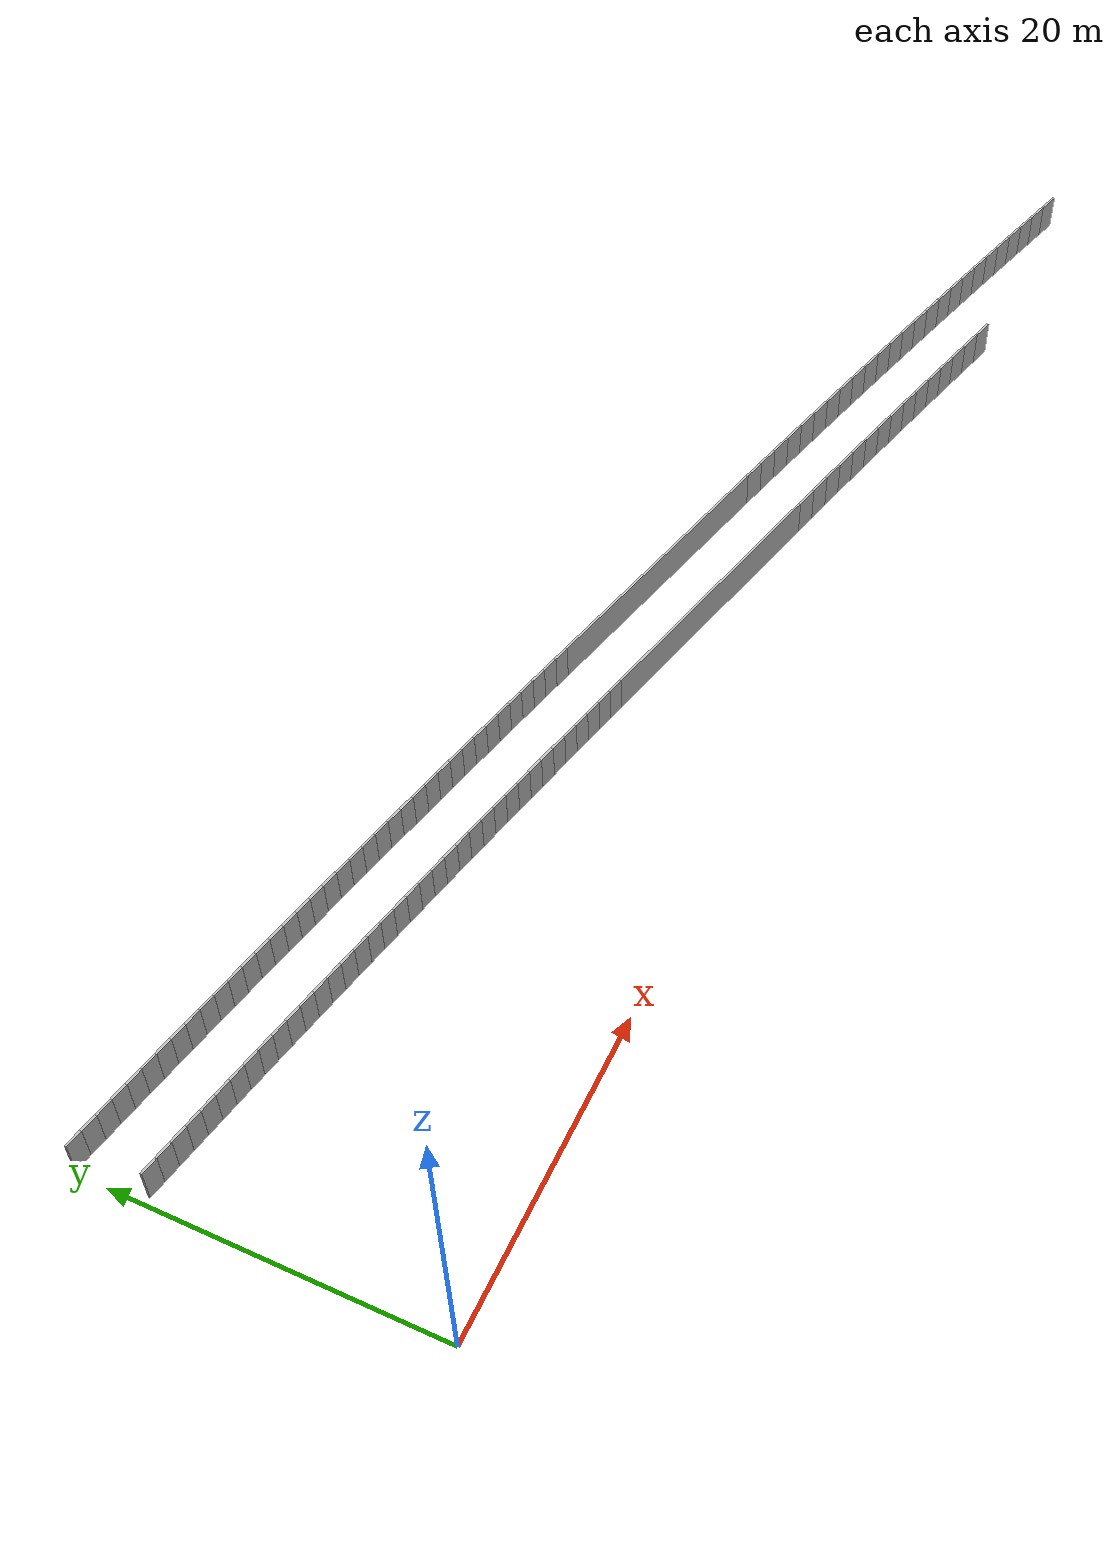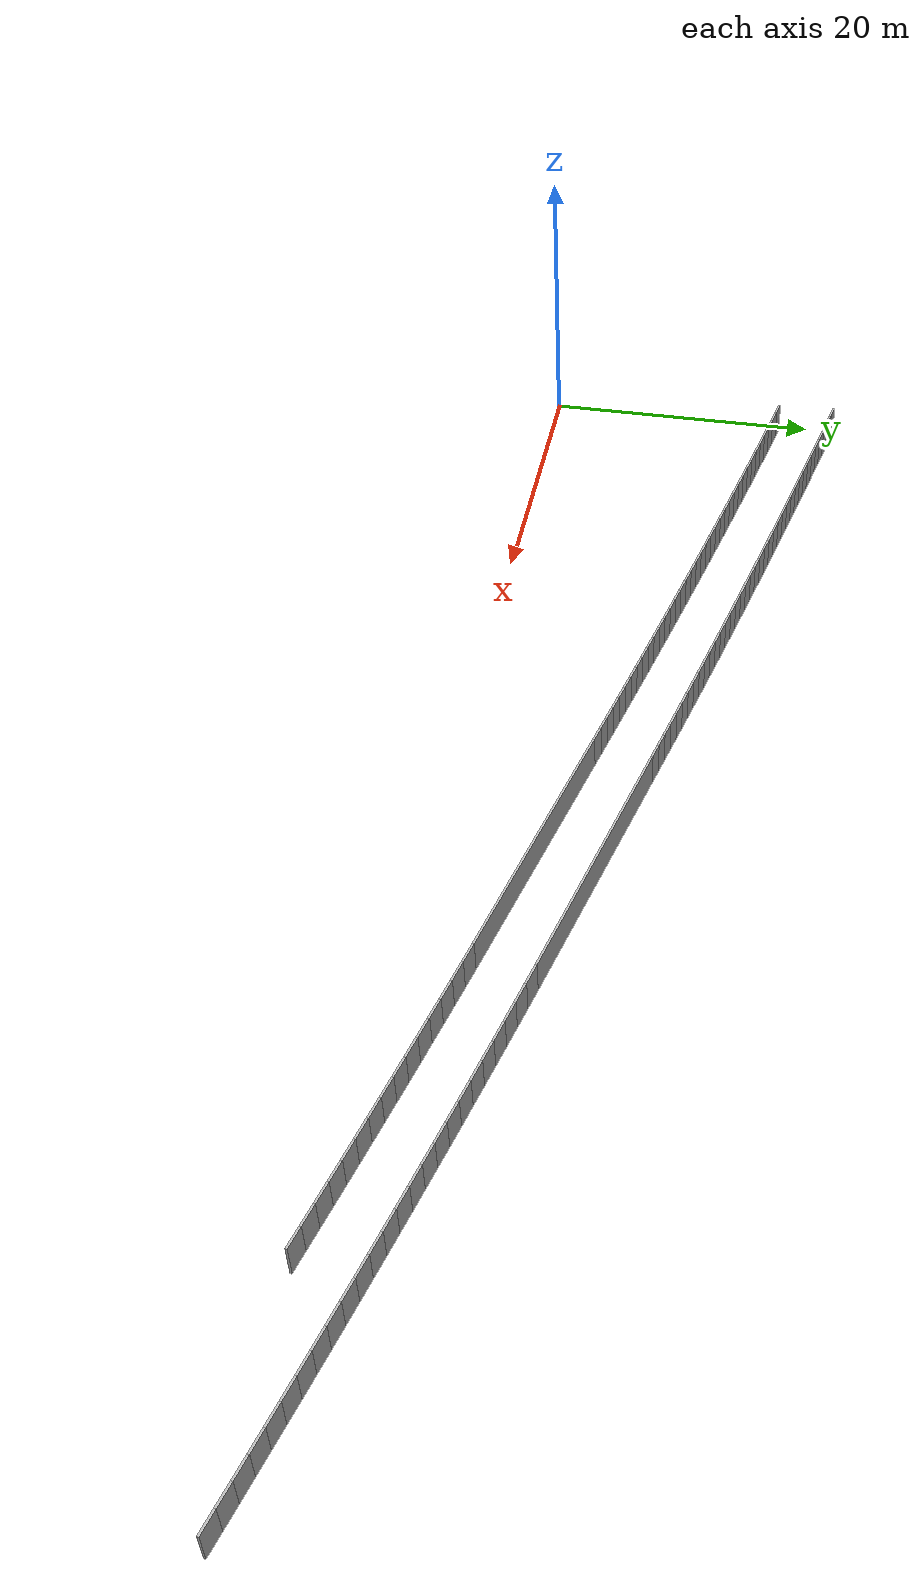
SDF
<?xml version="1.0" ?>
<sdf version="1.6">
  <model name="sps_1523">
    <pose frame="">0 0 0 0 -0 0</pose>
    <static>1</static>
    <self_collide>0</self_collide>
    <allow_auto_disable>0</allow_auto_disable>
    <link name="Wall318">
      <kinematic>0</kinematic>
      <gravity>1</gravity>
      <self_collide>0</self_collide>
      <collision name="collision">
        <geometry>
          <box>
            <size>18.671 0.15 2.5</size>
          </box>
        </geometry>
        <pose frame="">0 0 0 0 -0 0</pose>
      </collision>
      <visual name="visual">
        <geometry>
          <box>
            <size>18.671 0.15 2.5</size>
          </box>
        </geometry>
        <pose frame="">0 0 0 0 -0 0</pose>
        <cast_shadows>1</cast_shadows>
        <transparency>0.0</transparency>
      </visual>
      <pose frame="">48.5033 7.4247 1.25 0 -0 2.91246</pose>
    </link>
    <link name="Wall650">
      <kinematic>0</kinematic>
      <gravity>1</gravity>
      <self_collide>0</self_collide>
      <collision name="collision">
        <geometry>
          <box>
            <size>18.6821 0.15 2.5</size>
          </box>
        </geometry>
        <pose frame="">0 0 0 0 -0 0</pose>
      </collision>
      <visual name="visual">
        <geometry>
          <box>
            <size>18.6821 0.15 2.5</size>
          </box>
        </geometry>
        <pose frame="">0 0 0 0 -0 0</pose>
        <cast_shadows>1</cast_shadows>
        <transparency>0.0</transparency>
      </visual>
      <pose frame="">49.4523 11.4541 1.25 0 0 -0.229081</pose>
    </link>
    <link name="Wall8144">
      <kinematic>0</kinematic>
      <gravity>1</gravity>
      <self_collide>0</self_collide>
      <collision name="collision">
        <geometry>
          <box>
            <size>1.07591 0.15 2.5</size>
          </box>
        </geometry>
        <pose frame="">0 0 0 0 -0 0</pose>
      </collision>
      <visual name="visual">
        <geometry>
          <box>
            <size>1.07591 0.15 2.5</size>
          </box>
        </geometry>
        <pose frame="">0 0 0 0 -0 0</pose>
        <cast_shadows>1</cast_shadows>
        <transparency>0.0</transparency>
      </visual>
      <pose frame="">38.8879 9.66731 1.25 0 -0 2.91245</pose>
    </link>
    <link name="Wall8145">
      <kinematic>0</kinematic>
      <gravity>1</gravity>
      <self_collide>0</self_collide>
      <collision name="collision">
        <geometry>
          <box>
            <size>1.07587 0.15 2.5</size>
          </box>
        </geometry>
        <pose frame="">0 0 0 0 -0 0</pose>
      </collision>
      <visual name="visual">
        <geometry>
          <box>
            <size>1.07587 0.15 2.5</size>
          </box>
        </geometry>
        <pose frame="">0 0 0 0 -0 0</pose>
        <cast_shadows>1</cast_shadows>
        <transparency>0.0</transparency>
      </visual>
      <pose frame="">37.84 9.91121 1.25 0 -0 2.91337</pose>
    </link>
    <link name="Wall8146">
      <kinematic>0</kinematic>
      <gravity>1</gravity>
      <self_collide>0</self_collide>
      <collision name="collision">
        <geometry>
          <box>
            <size>1.07597 0.15 2.5</size>
          </box>
        </geometry>
        <pose frame="">0 0 0 0 -0 0</pose>
      </collision>
      <visual name="visual">
        <geometry>
          <box>
            <size>1.07597 0.15 2.5</size>
          </box>
        </geometry>
        <pose frame="">0 0 0 0 -0 0</pose>
        <cast_shadows>1</cast_shadows>
        <transparency>0.0</transparency>
      </visual>
      <pose frame="">36.7919 10.1539 1.25 0 -0 2.91473</pose>
    </link>
    <link name="Wall8147">
      <kinematic>0</kinematic>
      <gravity>1</gravity>
      <self_collide>0</self_collide>
      <collision name="collision">
        <geometry>
          <box>
            <size>1.07592 0.15 2.5</size>
          </box>
        </geometry>
        <pose frame="">0 0 0 0 -0 0</pose>
      </collision>
      <visual name="visual">
        <geometry>
          <box>
            <size>1.07592 0.15 2.5</size>
          </box>
        </geometry>
        <pose frame="">0 0 0 0 -0 0</pose>
        <cast_shadows>1</cast_shadows>
        <transparency>0.0</transparency>
      </visual>
      <pose frame="">35.7434 10.3954 1.25 0 -0 2.91571</pose>
    </link>
    <link name="Wall8148">
      <kinematic>0</kinematic>
      <gravity>1</gravity>
      <self_collide>0</self_collide>
      <collision name="collision">
        <geometry>
          <box>
            <size>1.07607 0.15 2.5</size>
          </box>
        </geometry>
        <pose frame="">0 0 0 0 -0 0</pose>
      </collision>
      <visual name="visual">
        <geometry>
          <box>
            <size>1.07607 0.15 2.5</size>
          </box>
        </geometry>
        <pose frame="">0 0 0 0 -0 0</pose>
        <cast_shadows>1</cast_shadows>
        <transparency>0.0</transparency>
      </visual>
      <pose frame="">34.6946 10.6358 1.25 0 -0 2.91685</pose>
    </link>
    <link name="Wall8149">
      <kinematic>0</kinematic>
      <gravity>1</gravity>
      <self_collide>0</self_collide>
      <collision name="collision">
        <geometry>
          <box>
            <size>1.07598 0.15 2.5</size>
          </box>
        </geometry>
        <pose frame="">0 0 0 0 -0 0</pose>
      </collision>
      <visual name="visual">
        <geometry>
          <box>
            <size>1.07598 0.15 2.5</size>
          </box>
        </geometry>
        <pose frame="">0 0 0 0 -0 0</pose>
        <cast_shadows>1</cast_shadows>
        <transparency>0.0</transparency>
      </visual>
      <pose frame="">33.6455 10.875 1.25 0 -0 2.918</pose>
    </link>
    <link name="Wall8150">
      <kinematic>0</kinematic>
      <gravity>1</gravity>
      <self_collide>0</self_collide>
      <collision name="collision">
        <geometry>
          <box>
            <size>1.07596 0.15 2.5</size>
          </box>
        </geometry>
        <pose frame="">0 0 0 0 -0 0</pose>
      </collision>
      <visual name="visual">
        <geometry>
          <box>
            <size>1.07596 0.15 2.5</size>
          </box>
        </geometry>
        <pose frame="">0 0 0 0 -0 0</pose>
        <cast_shadows>1</cast_shadows>
        <transparency>0.0</transparency>
      </visual>
      <pose frame="">32.5962 11.113 1.25 0 -0 2.9191</pose>
    </link>
    <link name="Wall8151">
      <kinematic>0</kinematic>
      <gravity>1</gravity>
      <self_collide>0</self_collide>
      <collision name="collision">
        <geometry>
          <box>
            <size>1.07581 0.15 2.5</size>
          </box>
        </geometry>
        <pose frame="">0 0 0 0 -0 0</pose>
      </collision>
      <visual name="visual">
        <geometry>
          <box>
            <size>1.07581 0.15 2.5</size>
          </box>
        </geometry>
        <pose frame="">0 0 0 0 -0 0</pose>
        <cast_shadows>1</cast_shadows>
        <transparency>0.0</transparency>
      </visual>
      <pose frame="">31.5467 11.3498 1.25 0 -0 2.92023</pose>
    </link>
    <link name="Wall8152">
      <kinematic>0</kinematic>
      <gravity>1</gravity>
      <self_collide>0</self_collide>
      <collision name="collision">
        <geometry>
          <box>
            <size>1.07596 0.15 2.5</size>
          </box>
        </geometry>
        <pose frame="">0 0 0 0 -0 0</pose>
      </collision>
      <visual name="visual">
        <geometry>
          <box>
            <size>1.07596 0.15 2.5</size>
          </box>
        </geometry>
        <pose frame="">0 0 0 0 -0 0</pose>
        <cast_shadows>1</cast_shadows>
        <transparency>0.0</transparency>
      </visual>
      <pose frame="">30.4969 11.5854 1.25 0 -0 2.92142</pose>
    </link>
    <link name="Wall8153">
      <kinematic>0</kinematic>
      <gravity>1</gravity>
      <self_collide>0</self_collide>
      <collision name="collision">
        <geometry>
          <box>
            <size>1.07595 0.15 2.5</size>
          </box>
        </geometry>
        <pose frame="">0 0 0 0 -0 0</pose>
      </collision>
      <visual name="visual">
        <geometry>
          <box>
            <size>1.07595 0.15 2.5</size>
          </box>
        </geometry>
        <pose frame="">0 0 0 0 -0 0</pose>
        <cast_shadows>1</cast_shadows>
        <transparency>0.0</transparency>
      </visual>
      <pose frame="">29.4468 11.8198 1.25 0 -0 2.92252</pose>
    </link>
    <link name="Wall8154">
      <kinematic>0</kinematic>
      <gravity>1</gravity>
      <self_collide>0</self_collide>
      <collision name="collision">
        <geometry>
          <box>
            <size>1.07603 0.15 2.5</size>
          </box>
        </geometry>
        <pose frame="">0 0 0 0 -0 0</pose>
      </collision>
      <visual name="visual">
        <geometry>
          <box>
            <size>1.07603 0.15 2.5</size>
          </box>
        </geometry>
        <pose frame="">0 0 0 0 -0 0</pose>
        <cast_shadows>1</cast_shadows>
        <transparency>0.0</transparency>
      </visual>
      <pose frame="">28.3964 12.053 1.25 0 -0 2.92376</pose>
    </link>
    <link name="Wall8155">
      <kinematic>0</kinematic>
      <gravity>1</gravity>
      <self_collide>0</self_collide>
      <collision name="collision">
        <geometry>
          <box>
            <size>1.07597 0.15 2.5</size>
          </box>
        </geometry>
        <pose frame="">0 0 0 0 -0 0</pose>
      </collision>
      <visual name="visual">
        <geometry>
          <box>
            <size>1.07597 0.15 2.5</size>
          </box>
        </geometry>
        <pose frame="">0 0 0 0 -0 0</pose>
        <cast_shadows>1</cast_shadows>
        <transparency>0.0</transparency>
      </visual>
      <pose frame="">27.3457 12.285 1.25 0 -0 2.92479</pose>
    </link>
    <link name="Wall8156">
      <kinematic>0</kinematic>
      <gravity>1</gravity>
      <self_collide>0</self_collide>
      <collision name="collision">
        <geometry>
          <box>
            <size>1.07593 0.15 2.5</size>
          </box>
        </geometry>
        <pose frame="">0 0 0 0 -0 0</pose>
      </collision>
      <visual name="visual">
        <geometry>
          <box>
            <size>1.07593 0.15 2.5</size>
          </box>
        </geometry>
        <pose frame="">0 0 0 0 -0 0</pose>
        <cast_shadows>1</cast_shadows>
        <transparency>0.0</transparency>
      </visual>
      <pose frame="">26.2948 12.5158 1.25 0 -0 2.92601</pose>
    </link>
    <link name="Wall8157">
      <kinematic>0</kinematic>
      <gravity>1</gravity>
      <self_collide>0</self_collide>
      <collision name="collision">
        <geometry>
          <box>
            <size>1.07586 0.15 2.5</size>
          </box>
        </geometry>
        <pose frame="">0 0 0 0 -0 0</pose>
      </collision>
      <visual name="visual">
        <geometry>
          <box>
            <size>1.07586 0.15 2.5</size>
          </box>
        </geometry>
        <pose frame="">0 0 0 0 -0 0</pose>
        <cast_shadows>1</cast_shadows>
        <transparency>0.0</transparency>
      </visual>
      <pose frame="">25.2436 12.7454 1.25 0 -0 2.9271</pose>
    </link>
    <link name="Wall8158">
      <kinematic>0</kinematic>
      <gravity>1</gravity>
      <self_collide>0</self_collide>
      <collision name="collision">
        <geometry>
          <box>
            <size>1.07601 0.15 2.5</size>
          </box>
        </geometry>
        <pose frame="">0 0 0 0 -0 0</pose>
      </collision>
      <visual name="visual">
        <geometry>
          <box>
            <size>1.07601 0.15 2.5</size>
          </box>
        </geometry>
        <pose frame="">0 0 0 0 -0 0</pose>
        <cast_shadows>1</cast_shadows>
        <transparency>0.0</transparency>
      </visual>
      <pose frame="">24.1923 12.9739 1.25 0 -0 2.92805</pose>
    </link>
    <link name="Wall8159">
      <kinematic>0</kinematic>
      <gravity>1</gravity>
      <self_collide>0</self_collide>
      <collision name="collision">
        <geometry>
          <box>
            <size>1.07594 0.15 2.5</size>
          </box>
        </geometry>
        <pose frame="">0 0 0 0 -0 0</pose>
      </collision>
      <visual name="visual">
        <geometry>
          <box>
            <size>1.07594 0.15 2.5</size>
          </box>
        </geometry>
        <pose frame="">0 0 0 0 -0 0</pose>
        <cast_shadows>1</cast_shadows>
        <transparency>0.0</transparency>
      </visual>
      <pose frame="">23.1406 13.2012 1.25 0 -0 2.92943</pose>
    </link>
    <link name="Wall8160">
      <kinematic>0</kinematic>
      <gravity>1</gravity>
      <self_collide>0</self_collide>
      <collision name="collision">
        <geometry>
          <box>
            <size>1.07606 0.15 2.5</size>
          </box>
        </geometry>
        <pose frame="">0 0 0 0 -0 0</pose>
      </collision>
      <visual name="visual">
        <geometry>
          <box>
            <size>1.07606 0.15 2.5</size>
          </box>
        </geometry>
        <pose frame="">0 0 0 0 -0 0</pose>
        <cast_shadows>1</cast_shadows>
        <transparency>0.0</transparency>
      </visual>
      <pose frame="">22.0886 13.4272 1.25 0 -0 2.93056</pose>
    </link>
    <link name="Wall8161">
      <kinematic>0</kinematic>
      <gravity>1</gravity>
      <self_collide>0</self_collide>
      <collision name="collision">
        <geometry>
          <box>
            <size>1.07582 0.15 2.5</size>
          </box>
        </geometry>
        <pose frame="">0 0 0 0 -0 0</pose>
      </collision>
      <visual name="visual">
        <geometry>
          <box>
            <size>1.07582 0.15 2.5</size>
          </box>
        </geometry>
        <pose frame="">0 0 0 0 -0 0</pose>
        <cast_shadows>1</cast_shadows>
        <transparency>0.0</transparency>
      </visual>
      <pose frame="">21.0364 13.652 1.25 0 -0 2.93161</pose>
    </link>
    <link name="Wall8162">
      <kinematic>0</kinematic>
      <gravity>1</gravity>
      <self_collide>0</self_collide>
      <collision name="collision">
        <geometry>
          <box>
            <size>1.07597 0.15 2.5</size>
          </box>
        </geometry>
        <pose frame="">0 0 0 0 -0 0</pose>
      </collision>
      <visual name="visual">
        <geometry>
          <box>
            <size>1.07597 0.15 2.5</size>
          </box>
        </geometry>
        <pose frame="">0 0 0 0 -0 0</pose>
        <cast_shadows>1</cast_shadows>
        <transparency>0.0</transparency>
      </visual>
      <pose frame="">19.984 13.8756 1.25 0 -0 2.93286</pose>
    </link>
    <link name="Wall8163">
      <kinematic>0</kinematic>
      <gravity>1</gravity>
      <self_collide>0</self_collide>
      <collision name="collision">
        <geometry>
          <box>
            <size>1.07609 0.15 2.5</size>
          </box>
        </geometry>
        <pose frame="">0 0 0 0 -0 0</pose>
      </collision>
      <visual name="visual">
        <geometry>
          <box>
            <size>1.07609 0.15 2.5</size>
          </box>
        </geometry>
        <pose frame="">0 0 0 0 -0 0</pose>
        <cast_shadows>1</cast_shadows>
        <transparency>0.0</transparency>
      </visual>
      <pose frame="">18.9312 14.098 1.25 0 -0 2.93399</pose>
    </link>
    <link name="Wall8164">
      <kinematic>0</kinematic>
      <gravity>1</gravity>
      <self_collide>0</self_collide>
      <collision name="collision">
        <geometry>
          <box>
            <size>1.07594 0.15 2.5</size>
          </box>
        </geometry>
        <pose frame="">0 0 0 0 -0 0</pose>
      </collision>
      <visual name="visual">
        <geometry>
          <box>
            <size>1.07594 0.15 2.5</size>
          </box>
        </geometry>
        <pose frame="">0 0 0 0 -0 0</pose>
        <cast_shadows>1</cast_shadows>
        <transparency>0.0</transparency>
      </visual>
      <pose frame="">17.8782 14.3193 1.25 0 -0 2.93489</pose>
    </link>
    <link name="Wall8165">
      <kinematic>0</kinematic>
      <gravity>1</gravity>
      <self_collide>0</self_collide>
      <collision name="collision">
        <geometry>
          <box>
            <size>1.07602 0.15 2.5</size>
          </box>
        </geometry>
        <pose frame="">0 0 0 0 -0 0</pose>
      </collision>
      <visual name="visual">
        <geometry>
          <box>
            <size>1.07602 0.15 2.5</size>
          </box>
        </geometry>
        <pose frame="">0 0 0 0 -0 0</pose>
        <cast_shadows>1</cast_shadows>
        <transparency>0.0</transparency>
      </visual>
      <pose frame="">16.8249 14.5394 1.25 0 -0 2.93623</pose>
    </link>
    <link name="Wall8166">
      <kinematic>0</kinematic>
      <gravity>1</gravity>
      <self_collide>0</self_collide>
      <collision name="collision">
        <geometry>
          <box>
            <size>1.07593 0.15 2.5</size>
          </box>
        </geometry>
        <pose frame="">0 0 0 0 -0 0</pose>
      </collision>
      <visual name="visual">
        <geometry>
          <box>
            <size>1.07593 0.15 2.5</size>
          </box>
        </geometry>
        <pose frame="">0 0 0 0 -0 0</pose>
        <cast_shadows>1</cast_shadows>
        <transparency>0.0</transparency>
      </visual>
      <pose frame="">15.7714 14.7582 1.25 0 -0 2.93743</pose>
    </link>
    <link name="Wall8167">
      <kinematic>0</kinematic>
      <gravity>1</gravity>
      <self_collide>0</self_collide>
      <collision name="collision">
        <geometry>
          <box>
            <size>1.07589 0.15 2.5</size>
          </box>
        </geometry>
        <pose frame="">0 0 0 0 -0 0</pose>
      </collision>
      <visual name="visual">
        <geometry>
          <box>
            <size>1.07589 0.15 2.5</size>
          </box>
        </geometry>
        <pose frame="">0 0 0 0 -0 0</pose>
        <cast_shadows>1</cast_shadows>
        <transparency>0.0</transparency>
      </visual>
      <pose frame="">14.7178 14.9758 1.25 0 -0 2.93847</pose>
    </link>
    <link name="Wall8168">
      <kinematic>0</kinematic>
      <gravity>1</gravity>
      <self_collide>0</self_collide>
      <collision name="collision">
        <geometry>
          <box>
            <size>1.07605 0.15 2.5</size>
          </box>
        </geometry>
        <pose frame="">0 0 0 0 -0 0</pose>
      </collision>
      <visual name="visual">
        <geometry>
          <box>
            <size>1.07605 0.15 2.5</size>
          </box>
        </geometry>
        <pose frame="">0 0 0 0 -0 0</pose>
        <cast_shadows>1</cast_shadows>
        <transparency>0.0</transparency>
      </visual>
      <pose frame="">13.6638 15.1922 1.25 0 -0 2.93971</pose>
    </link>
    <link name="Wall8169">
      <kinematic>0</kinematic>
      <gravity>1</gravity>
      <self_collide>0</self_collide>
      <collision name="collision">
        <geometry>
          <box>
            <size>1.07606 0.15 2.5</size>
          </box>
        </geometry>
        <pose frame="">0 0 0 0 -0 0</pose>
      </collision>
      <visual name="visual">
        <geometry>
          <box>
            <size>1.07606 0.15 2.5</size>
          </box>
        </geometry>
        <pose frame="">0 0 0 0 -0 0</pose>
        <cast_shadows>1</cast_shadows>
        <transparency>0.0</transparency>
      </visual>
      <pose frame="">12.6095 15.4074 1.25 0 -0 2.94082</pose>
    </link>
    <link name="Wall8170">
      <kinematic>0</kinematic>
      <gravity>1</gravity>
      <self_collide>0</self_collide>
      <collision name="collision">
        <geometry>
          <box>
            <size>1.07577 0.15 2.5</size>
          </box>
        </geometry>
        <pose frame="">0 0 0 0 -0 0</pose>
      </collision>
      <visual name="visual">
        <geometry>
          <box>
            <size>1.07577 0.15 2.5</size>
          </box>
        </geometry>
        <pose frame="">0 0 0 0 -0 0</pose>
        <cast_shadows>1</cast_shadows>
        <transparency>0.0</transparency>
      </visual>
      <pose frame="">11.555 15.6214 1.25 0 -0 2.94186</pose>
    </link>
    <link name="Wall8171">
      <kinematic>0</kinematic>
      <gravity>1</gravity>
      <self_collide>0</self_collide>
      <collision name="collision">
        <geometry>
          <box>
            <size>1.07616 0.15 2.5</size>
          </box>
        </geometry>
        <pose frame="">0 0 0 0 -0 0</pose>
      </collision>
      <visual name="visual">
        <geometry>
          <box>
            <size>1.07616 0.15 2.5</size>
          </box>
        </geometry>
        <pose frame="">0 0 0 0 -0 0</pose>
        <cast_shadows>1</cast_shadows>
        <transparency>0.0</transparency>
      </visual>
      <pose frame="">10.5004 15.8343 1.25 0 -0 2.94292</pose>
    </link>
    <link name="Wall8172">
      <kinematic>0</kinematic>
      <gravity>1</gravity>
      <self_collide>0</self_collide>
      <collision name="collision">
        <geometry>
          <box>
            <size>1.07589 0.15 2.5</size>
          </box>
        </geometry>
        <pose frame="">0 0 0 0 -0 0</pose>
      </collision>
      <visual name="visual">
        <geometry>
          <box>
            <size>1.07589 0.15 2.5</size>
          </box>
        </geometry>
        <pose frame="">0 0 0 0 -0 0</pose>
        <cast_shadows>1</cast_shadows>
        <transparency>0.0</transparency>
      </visual>
      <pose frame="">9.44537 16.046 1.25 0 -0 2.9442</pose>
    </link>
    <link name="Wall8173">
      <kinematic>0</kinematic>
      <gravity>1</gravity>
      <self_collide>0</self_collide>
      <collision name="collision">
        <geometry>
          <box>
            <size>1.07607 0.15 2.5</size>
          </box>
        </geometry>
        <pose frame="">0 0 0 0 -0 0</pose>
      </collision>
      <visual name="visual">
        <geometry>
          <box>
            <size>1.07607 0.15 2.5</size>
          </box>
        </geometry>
        <pose frame="">0 0 0 0 -0 0</pose>
        <cast_shadows>1</cast_shadows>
        <transparency>0.0</transparency>
      </visual>
      <pose frame="">8.39016 16.2564 1.25 0 -0 2.94539</pose>
    </link>
    <link name="Wall8174">
      <kinematic>0</kinematic>
      <gravity>1</gravity>
      <self_collide>0</self_collide>
      <collision name="collision">
        <geometry>
          <box>
            <size>1.07584 0.15 2.5</size>
          </box>
        </geometry>
        <pose frame="">0 0 0 0 -0 0</pose>
      </collision>
      <visual name="visual">
        <geometry>
          <box>
            <size>1.07584 0.15 2.5</size>
          </box>
        </geometry>
        <pose frame="">0 0 0 0 -0 0</pose>
        <cast_shadows>1</cast_shadows>
        <transparency>0.0</transparency>
      </visual>
      <pose frame="">7.33474 16.4656 1.25 0 -0 2.94644</pose>
    </link>
    <link name="Wall8175">
      <kinematic>0</kinematic>
      <gravity>1</gravity>
      <self_collide>0</self_collide>
      <collision name="collision">
        <geometry>
          <box>
            <size>1.07596 0.15 2.5</size>
          </box>
        </geometry>
        <pose frame="">0 0 0 0 -0 0</pose>
      </collision>
      <visual name="visual">
        <geometry>
          <box>
            <size>1.07596 0.15 2.5</size>
          </box>
        </geometry>
        <pose frame="">0 0 0 0 -0 0</pose>
        <cast_shadows>1</cast_shadows>
        <transparency>0.0</transparency>
      </visual>
      <pose frame="">6.27914 16.6736 1.25 0 -0 2.94762</pose>
    </link>
    <link name="Wall8176">
      <kinematic>0</kinematic>
      <gravity>1</gravity>
      <self_collide>0</self_collide>
      <collision name="collision">
        <geometry>
          <box>
            <size>1.07591 0.15 2.5</size>
          </box>
        </geometry>
        <pose frame="">0 0 0 0 -0 0</pose>
      </collision>
      <visual name="visual">
        <geometry>
          <box>
            <size>1.07591 0.15 2.5</size>
          </box>
        </geometry>
        <pose frame="">0 0 0 0 -0 0</pose>
        <cast_shadows>1</cast_shadows>
        <transparency>0.0</transparency>
      </visual>
      <pose frame="">5.22326 16.8804 1.25 0 -0 2.94877</pose>
    </link>
    <link name="Wall8177">
      <kinematic>0</kinematic>
      <gravity>1</gravity>
      <self_collide>0</self_collide>
      <collision name="collision">
        <geometry>
          <box>
            <size>1.07593 0.15 2.5</size>
          </box>
        </geometry>
        <pose frame="">0 0 0 0 -0 0</pose>
      </collision>
      <visual name="visual">
        <geometry>
          <box>
            <size>1.07593 0.15 2.5</size>
          </box>
        </geometry>
        <pose frame="">0 0 0 0 -0 0</pose>
        <cast_shadows>1</cast_shadows>
        <transparency>0.0</transparency>
      </visual>
      <pose frame="">4.16717 17.086 1.25 0 -0 2.94987</pose>
    </link>
    <link name="Wall8178">
      <kinematic>0</kinematic>
      <gravity>1</gravity>
      <self_collide>0</self_collide>
      <collision name="collision">
        <geometry>
          <box>
            <size>1.07609 0.15 2.5</size>
          </box>
        </geometry>
        <pose frame="">0 0 0 0 -0 0</pose>
      </collision>
      <visual name="visual">
        <geometry>
          <box>
            <size>1.07609 0.15 2.5</size>
          </box>
        </geometry>
        <pose frame="">0 0 0 0 -0 0</pose>
        <cast_shadows>1</cast_shadows>
        <transparency>0.0</transparency>
      </visual>
      <pose frame="">3.11077 17.2905 1.25 0 -0 2.95088</pose>
    </link>
    <link name="Wall8179">
      <kinematic>0</kinematic>
      <gravity>1</gravity>
      <self_collide>0</self_collide>
      <collision name="collision">
        <geometry>
          <box>
            <size>1.0759 0.15 2.5</size>
          </box>
        </geometry>
        <pose frame="">0 0 0 0 -0 0</pose>
      </collision>
      <visual name="visual">
        <geometry>
          <box>
            <size>1.0759 0.15 2.5</size>
          </box>
        </geometry>
        <pose frame="">0 0 0 0 -0 0</pose>
        <cast_shadows>1</cast_shadows>
        <transparency>0.0</transparency>
      </visual>
      <pose frame="">2.05416 17.4938 1.25 0 -0 2.95212</pose>
    </link>
    <link name="Wall8180">
      <kinematic>0</kinematic>
      <gravity>1</gravity>
      <self_collide>0</self_collide>
      <collision name="collision">
        <geometry>
          <box>
            <size>1.07603 0.15 2.5</size>
          </box>
        </geometry>
        <pose frame="">0 0 0 0 -0 0</pose>
      </collision>
      <visual name="visual">
        <geometry>
          <box>
            <size>1.07603 0.15 2.5</size>
          </box>
        </geometry>
        <pose frame="">0 0 0 0 -0 0</pose>
        <cast_shadows>1</cast_shadows>
        <transparency>0.0</transparency>
      </visual>
      <pose frame="">0.997337 17.6958 1.25 0 -0 2.9533</pose>
    </link>
    <link name="Wall9109">
      <kinematic>0</kinematic>
      <gravity>1</gravity>
      <self_collide>0</self_collide>
      <collision name="collision">
        <geometry>
          <box>
            <size>1.08065 0.15 2.5</size>
          </box>
        </geometry>
        <pose frame="">0 0 0 0 -0 0</pose>
      </collision>
      <visual name="visual">
        <geometry>
          <box>
            <size>1.08065 0.15 2.5</size>
          </box>
        </geometry>
        <pose frame="">0 0 0 0 -0 0</pose>
        <cast_shadows>1</cast_shadows>
        <transparency>0.0</transparency>
      </visual>
      <pose frame="">39.8291 13.6981 1.25 0 -0 2.91231</pose>
    </link>
    <link name="Wall9110">
      <kinematic>0</kinematic>
      <gravity>1</gravity>
      <self_collide>0</self_collide>
      <collision name="collision">
        <geometry>
          <box>
            <size>1.08062 0.15 2.5</size>
          </box>
        </geometry>
        <pose frame="">0 0 0 0 -0 0</pose>
      </collision>
      <visual name="visual">
        <geometry>
          <box>
            <size>1.08062 0.15 2.5</size>
          </box>
        </geometry>
        <pose frame="">0 0 0 0 -0 0</pose>
        <cast_shadows>1</cast_shadows>
        <transparency>0.0</transparency>
      </visual>
      <pose frame="">38.7766 13.9431 1.25 0 -0 2.91341</pose>
    </link>
    <link name="Wall9111">
      <kinematic>0</kinematic>
      <gravity>1</gravity>
      <self_collide>0</self_collide>
      <collision name="collision">
        <geometry>
          <box>
            <size>1.08075 0.15 2.5</size>
          </box>
        </geometry>
        <pose frame="">0 0 0 0 -0 0</pose>
      </collision>
      <visual name="visual">
        <geometry>
          <box>
            <size>1.08075 0.15 2.5</size>
          </box>
        </geometry>
        <pose frame="">0 0 0 0 -0 0</pose>
        <cast_shadows>1</cast_shadows>
        <transparency>0.0</transparency>
      </visual>
      <pose frame="">37.7237 14.1869 1.25 0 -0 2.91465</pose>
    </link>
    <link name="Wall9112">
      <kinematic>0</kinematic>
      <gravity>1</gravity>
      <self_collide>0</self_collide>
      <collision name="collision">
        <geometry>
          <box>
            <size>1.08061 0.15 2.5</size>
          </box>
        </geometry>
        <pose frame="">0 0 0 0 -0 0</pose>
      </collision>
      <visual name="visual">
        <geometry>
          <box>
            <size>1.08061 0.15 2.5</size>
          </box>
        </geometry>
        <pose frame="">0 0 0 0 -0 0</pose>
        <cast_shadows>1</cast_shadows>
        <transparency>0.0</transparency>
      </visual>
      <pose frame="">36.6706 14.4295 1.25 0 -0 2.91573</pose>
    </link>
    <link name="Wall9113">
      <kinematic>0</kinematic>
      <gravity>1</gravity>
      <self_collide>0</self_collide>
      <collision name="collision">
        <geometry>
          <box>
            <size>1.08075 0.15 2.5</size>
          </box>
        </geometry>
        <pose frame="">0 0 0 0 -0 0</pose>
      </collision>
      <visual name="visual">
        <geometry>
          <box>
            <size>1.08075 0.15 2.5</size>
          </box>
        </geometry>
        <pose frame="">0 0 0 0 -0 0</pose>
        <cast_shadows>1</cast_shadows>
        <transparency>0.0</transparency>
      </visual>
      <pose frame="">35.6173 14.6709 1.25 0 -0 2.91691</pose>
    </link>
    <link name="Wall9114">
      <kinematic>0</kinematic>
      <gravity>1</gravity>
      <self_collide>0</self_collide>
      <collision name="collision">
        <geometry>
          <box>
            <size>1.08073 0.15 2.5</size>
          </box>
        </geometry>
        <pose frame="">0 0 0 0 -0 0</pose>
      </collision>
      <visual name="visual">
        <geometry>
          <box>
            <size>1.08073 0.15 2.5</size>
          </box>
        </geometry>
        <pose frame="">0 0 0 0 -0 0</pose>
        <cast_shadows>1</cast_shadows>
        <transparency>0.0</transparency>
      </visual>
      <pose frame="">34.5636 14.9111 1.25 0 -0 2.91801</pose>
    </link>
    <link name="Wall9115">
      <kinematic>0</kinematic>
      <gravity>1</gravity>
      <self_collide>0</self_collide>
      <collision name="collision">
        <geometry>
          <box>
            <size>1.08064 0.15 2.5</size>
          </box>
        </geometry>
        <pose frame="">0 0 0 0 -0 0</pose>
      </collision>
      <visual name="visual">
        <geometry>
          <box>
            <size>1.08064 0.15 2.5</size>
          </box>
        </geometry>
        <pose frame="">0 0 0 0 -0 0</pose>
        <cast_shadows>1</cast_shadows>
        <transparency>0.0</transparency>
      </visual>
      <pose frame="">33.5096 15.1501 1.25 0 -0 2.91915</pose>
    </link>
    <link name="Wall9116">
      <kinematic>0</kinematic>
      <gravity>1</gravity>
      <self_collide>0</self_collide>
      <collision name="collision">
        <geometry>
          <box>
            <size>1.08055 0.15 2.5</size>
          </box>
        </geometry>
        <pose frame="">0 0 0 0 -0 0</pose>
      </collision>
      <visual name="visual">
        <geometry>
          <box>
            <size>1.08055 0.15 2.5</size>
          </box>
        </geometry>
        <pose frame="">0 0 0 0 -0 0</pose>
        <cast_shadows>1</cast_shadows>
        <transparency>0.0</transparency>
      </visual>
      <pose frame="">32.4555 15.3879 1.25 0 -0 2.92029</pose>
    </link>
    <link name="Wall9117">
      <kinematic>0</kinematic>
      <gravity>1</gravity>
      <self_collide>0</self_collide>
      <collision name="collision">
        <geometry>
          <box>
            <size>1.08083 0.15 2.5</size>
          </box>
        </geometry>
        <pose frame="">0 0 0 0 -0 0</pose>
      </collision>
      <visual name="visual">
        <geometry>
          <box>
            <size>1.08083 0.15 2.5</size>
          </box>
        </geometry>
        <pose frame="">0 0 0 0 -0 0</pose>
        <cast_shadows>1</cast_shadows>
        <transparency>0.0</transparency>
      </visual>
      <pose frame="">31.4011 15.6245 1.25 0 -0 2.92145</pose>
    </link>
    <link name="Wall9118">
      <kinematic>0</kinematic>
      <gravity>1</gravity>
      <self_collide>0</self_collide>
      <collision name="collision">
        <geometry>
          <box>
            <size>1.08067 0.15 2.5</size>
          </box>
        </geometry>
        <pose frame="">0 0 0 0 -0 0</pose>
      </collision>
      <visual name="visual">
        <geometry>
          <box>
            <size>1.08067 0.15 2.5</size>
          </box>
        </geometry>
        <pose frame="">0 0 0 0 -0 0</pose>
        <cast_shadows>1</cast_shadows>
        <transparency>0.0</transparency>
      </visual>
      <pose frame="">30.3463 15.86 1.25 0 -0 2.9224</pose>
    </link>
    <link name="Wall9119">
      <kinematic>0</kinematic>
      <gravity>1</gravity>
      <self_collide>0</self_collide>
      <collision name="collision">
        <geometry>
          <box>
            <size>1.08054 0.15 2.5</size>
          </box>
        </geometry>
        <pose frame="">0 0 0 0 -0 0</pose>
      </collision>
      <visual name="visual">
        <geometry>
          <box>
            <size>1.08054 0.15 2.5</size>
          </box>
        </geometry>
        <pose frame="">0 0 0 0 -0 0</pose>
        <cast_shadows>1</cast_shadows>
        <transparency>0.0</transparency>
      </visual>
      <pose frame="">29.2914 16.0943 1.25 0 -0 2.9237</pose>
    </link>
    <link name="Wall9120">
      <kinematic>0</kinematic>
      <gravity>1</gravity>
      <self_collide>0</self_collide>
      <collision name="collision">
        <geometry>
          <box>
            <size>1.08071 0.15 2.5</size>
          </box>
        </geometry>
        <pose frame="">0 0 0 0 -0 0</pose>
      </collision>
      <visual name="visual">
        <geometry>
          <box>
            <size>1.08071 0.15 2.5</size>
          </box>
        </geometry>
        <pose frame="">0 0 0 0 -0 0</pose>
        <cast_shadows>1</cast_shadows>
        <transparency>0.0</transparency>
      </visual>
      <pose frame="">28.2362 16.3273 1.25 0 -0 2.92483</pose>
    </link>
    <link name="Wall9121">
      <kinematic>0</kinematic>
      <gravity>1</gravity>
      <self_collide>0</self_collide>
      <collision name="collision">
        <geometry>
          <box>
            <size>1.08063 0.15 2.5</size>
          </box>
        </geometry>
        <pose frame="">0 0 0 0 -0 0</pose>
      </collision>
      <visual name="visual">
        <geometry>
          <box>
            <size>1.08063 0.15 2.5</size>
          </box>
        </geometry>
        <pose frame="">0 0 0 0 -0 0</pose>
        <cast_shadows>1</cast_shadows>
        <transparency>0.0</transparency>
      </visual>
      <pose frame="">27.1807 16.5591 1.25 0 -0 2.92597</pose>
    </link>
    <link name="Wall9122">
      <kinematic>0</kinematic>
      <gravity>1</gravity>
      <self_collide>0</self_collide>
      <collision name="collision">
        <geometry>
          <box>
            <size>1.08072 0.15 2.5</size>
          </box>
        </geometry>
        <pose frame="">0 0 0 0 -0 0</pose>
      </collision>
      <visual name="visual">
        <geometry>
          <box>
            <size>1.08072 0.15 2.5</size>
          </box>
        </geometry>
        <pose frame="">0 0 0 0 -0 0</pose>
        <cast_shadows>1</cast_shadows>
        <transparency>0.0</transparency>
      </visual>
      <pose frame="">26.1249 16.7897 1.25 0 -0 2.92715</pose>
    </link>
    <link name="Wall9123">
      <kinematic>0</kinematic>
      <gravity>1</gravity>
      <self_collide>0</self_collide>
      <collision name="collision">
        <geometry>
          <box>
            <size>1.08072 0.15 2.5</size>
          </box>
        </geometry>
        <pose frame="">0 0 0 0 -0 0</pose>
      </collision>
      <visual name="visual">
        <geometry>
          <box>
            <size>1.08072 0.15 2.5</size>
          </box>
        </geometry>
        <pose frame="">0 0 0 0 -0 0</pose>
        <cast_shadows>1</cast_shadows>
        <transparency>0.0</transparency>
      </visual>
      <pose frame="">25.0688 17.0191 1.25 0 -0 2.92825</pose>
    </link>
    <link name="Wall9124">
      <kinematic>0</kinematic>
      <gravity>1</gravity>
      <self_collide>0</self_collide>
      <collision name="collision">
        <geometry>
          <box>
            <size>1.08064 0.15 2.5</size>
          </box>
        </geometry>
        <pose frame="">0 0 0 0 -0 0</pose>
      </collision>
      <visual name="visual">
        <geometry>
          <box>
            <size>1.08064 0.15 2.5</size>
          </box>
        </geometry>
        <pose frame="">0 0 0 0 -0 0</pose>
        <cast_shadows>1</cast_shadows>
        <transparency>0.0</transparency>
      </visual>
      <pose frame="">24.0125 17.2473 1.25 0 -0 2.92939</pose>
    </link>
    <link name="Wall9125">
      <kinematic>0</kinematic>
      <gravity>1</gravity>
      <self_collide>0</self_collide>
      <collision name="collision">
        <geometry>
          <box>
            <size>1.08085 0.15 2.5</size>
          </box>
        </geometry>
        <pose frame="">0 0 0 0 -0 0</pose>
      </collision>
      <visual name="visual">
        <geometry>
          <box>
            <size>1.08085 0.15 2.5</size>
          </box>
        </geometry>
        <pose frame="">0 0 0 0 -0 0</pose>
        <cast_shadows>1</cast_shadows>
        <transparency>0.0</transparency>
      </visual>
      <pose frame="">22.9559 17.4744 1.25 0 -0 2.93035</pose>
    </link>
    <link name="Wall9126">
      <kinematic>0</kinematic>
      <gravity>1</gravity>
      <self_collide>0</self_collide>
      <collision name="collision">
        <geometry>
          <box>
            <size>1.08072 0.15 2.5</size>
          </box>
        </geometry>
        <pose frame="">0 0 0 0 -0 0</pose>
      </collision>
      <visual name="visual">
        <geometry>
          <box>
            <size>1.08072 0.15 2.5</size>
          </box>
        </geometry>
        <pose frame="">0 0 0 0 -0 0</pose>
        <cast_shadows>1</cast_shadows>
        <transparency>0.0</transparency>
      </visual>
      <pose frame="">21.8989 17.7003 1.25 0 -0 2.93171</pose>
    </link>
    <link name="Wall9127">
      <kinematic>0</kinematic>
      <gravity>1</gravity>
      <self_collide>0</self_collide>
      <collision name="collision">
        <geometry>
          <box>
            <size>1.08048 0.15 2.5</size>
          </box>
        </geometry>
        <pose frame="">0 0 0 0 -0 0</pose>
      </collision>
      <visual name="visual">
        <geometry>
          <box>
            <size>1.08048 0.15 2.5</size>
          </box>
        </geometry>
        <pose frame="">0 0 0 0 -0 0</pose>
        <cast_shadows>1</cast_shadows>
        <transparency>0.0</transparency>
      </visual>
      <pose frame="">20.8419 17.9249 1.25 0 -0 2.93276</pose>
    </link>
    <link name="Wall9128">
      <kinematic>0</kinematic>
      <gravity>1</gravity>
      <self_collide>0</self_collide>
      <collision name="collision">
        <geometry>
          <box>
            <size>1.08078 0.15 2.5</size>
          </box>
        </geometry>
        <pose frame="">0 0 0 0 -0 0</pose>
      </collision>
      <visual name="visual">
        <geometry>
          <box>
            <size>1.08078 0.15 2.5</size>
          </box>
        </geometry>
        <pose frame="">0 0 0 0 -0 0</pose>
        <cast_shadows>1</cast_shadows>
        <transparency>0.0</transparency>
      </visual>
      <pose frame="">19.7847 18.1483 1.25 0 -0 2.93392</pose>
    </link>
    <link name="Wall9129">
      <kinematic>0</kinematic>
      <gravity>1</gravity>
      <self_collide>0</self_collide>
      <collision name="collision">
        <geometry>
          <box>
            <size>1.08057 0.15 2.5</size>
          </box>
        </geometry>
        <pose frame="">0 0 0 0 -0 0</pose>
      </collision>
      <visual name="visual">
        <geometry>
          <box>
            <size>1.08057 0.15 2.5</size>
          </box>
        </geometry>
        <pose frame="">0 0 0 0 -0 0</pose>
        <cast_shadows>1</cast_shadows>
        <transparency>0.0</transparency>
      </visual>
      <pose frame="">18.7271 18.3705 1.25 0 -0 2.93509</pose>
    </link>
    <link name="Wall9130">
      <kinematic>0</kinematic>
      <gravity>1</gravity>
      <self_collide>0</self_collide>
      <collision name="collision">
        <geometry>
          <box>
            <size>1.0807 0.15 2.5</size>
          </box>
        </geometry>
        <pose frame="">0 0 0 0 -0 0</pose>
      </collision>
      <visual name="visual">
        <geometry>
          <box>
            <size>1.0807 0.15 2.5</size>
          </box>
        </geometry>
        <pose frame="">0 0 0 0 -0 0</pose>
        <cast_shadows>1</cast_shadows>
        <transparency>0.0</transparency>
      </visual>
      <pose frame="">17.6693 18.5915 1.25 0 -0 2.93621</pose>
    </link>
    <link name="Wall9131">
      <kinematic>0</kinematic>
      <gravity>1</gravity>
      <self_collide>0</self_collide>
      <collision name="collision">
        <geometry>
          <box>
            <size>1.0807 0.15 2.5</size>
          </box>
        </geometry>
        <pose frame="">0 0 0 0 -0 0</pose>
      </collision>
      <visual name="visual">
        <geometry>
          <box>
            <size>1.0807 0.15 2.5</size>
          </box>
        </geometry>
        <pose frame="">0 0 0 0 -0 0</pose>
        <cast_shadows>1</cast_shadows>
        <transparency>0.0</transparency>
      </visual>
      <pose frame="">16.6112 18.8113 1.25 0 -0 2.93731</pose>
    </link>
    <link name="Wall9132">
      <kinematic>0</kinematic>
      <gravity>1</gravity>
      <self_collide>0</self_collide>
      <collision name="collision">
        <geometry>
          <box>
            <size>1.08062 0.15 2.5</size>
          </box>
        </geometry>
        <pose frame="">0 0 0 0 -0 0</pose>
      </collision>
      <visual name="visual">
        <geometry>
          <box>
            <size>1.08062 0.15 2.5</size>
          </box>
        </geometry>
        <pose frame="">0 0 0 0 -0 0</pose>
        <cast_shadows>1</cast_shadows>
        <transparency>0.0</transparency>
      </visual>
      <pose frame="">15.5528 19.0299 1.25 0 -0 2.9385</pose>
    </link>
    <link name="Wall9133">
      <kinematic>0</kinematic>
      <gravity>1</gravity>
      <self_collide>0</self_collide>
      <collision name="collision">
        <geometry>
          <box>
            <size>1.08074 0.15 2.5</size>
          </box>
        </geometry>
        <pose frame="">0 0 0 0 -0 0</pose>
      </collision>
      <visual name="visual">
        <geometry>
          <box>
            <size>1.08074 0.15 2.5</size>
          </box>
        </geometry>
        <pose frame="">0 0 0 0 -0 0</pose>
        <cast_shadows>1</cast_shadows>
        <transparency>0.0</transparency>
      </visual>
      <pose frame="">14.4943 19.2473 1.25 0 -0 2.93962</pose>
    </link>
    <link name="Wall9134">
      <kinematic>0</kinematic>
      <gravity>1</gravity>
      <self_collide>0</self_collide>
      <collision name="collision">
        <geometry>
          <box>
            <size>1.08072 0.15 2.5</size>
          </box>
        </geometry>
        <pose frame="">0 0 0 0 -0 0</pose>
      </collision>
      <visual name="visual">
        <geometry>
          <box>
            <size>1.08072 0.15 2.5</size>
          </box>
        </geometry>
        <pose frame="">0 0 0 0 -0 0</pose>
        <cast_shadows>1</cast_shadows>
        <transparency>0.0</transparency>
      </visual>
      <pose frame="">13.4354 19.4634 1.25 0 -0 2.94089</pose>
    </link>
    <link name="Wall9135">
      <kinematic>0</kinematic>
      <gravity>1</gravity>
      <self_collide>0</self_collide>
      <collision name="collision">
        <geometry>
          <box>
            <size>1.08068 0.15 2.5</size>
          </box>
        </geometry>
        <pose frame="">0 0 0 0 -0 0</pose>
      </collision>
      <visual name="visual">
        <geometry>
          <box>
            <size>1.08068 0.15 2.5</size>
          </box>
        </geometry>
        <pose frame="">0 0 0 0 -0 0</pose>
        <cast_shadows>1</cast_shadows>
        <transparency>0.0</transparency>
      </visual>
      <pose frame="">12.3762 19.6783 1.25 0 -0 2.94192</pose>
    </link>
    <link name="Wall9136">
      <kinematic>0</kinematic>
      <gravity>1</gravity>
      <self_collide>0</self_collide>
      <collision name="collision">
        <geometry>
          <box>
            <size>1.08063 0.15 2.5</size>
          </box>
        </geometry>
        <pose frame="">0 0 0 0 -0 0</pose>
      </collision>
      <visual name="visual">
        <geometry>
          <box>
            <size>1.08063 0.15 2.5</size>
          </box>
        </geometry>
        <pose frame="">0 0 0 0 -0 0</pose>
        <cast_shadows>1</cast_shadows>
        <transparency>0.0</transparency>
      </visual>
      <pose frame="">11.3169 19.8921 1.25 0 -0 2.943</pose>
    </link>
    <link name="Wall9137">
      <kinematic>0</kinematic>
      <gravity>1</gravity>
      <self_collide>0</self_collide>
      <collision name="collision">
        <geometry>
          <box>
            <size>1.08082 0.15 2.5</size>
          </box>
        </geometry>
        <pose frame="">0 0 0 0 -0 0</pose>
      </collision>
      <visual name="visual">
        <geometry>
          <box>
            <size>1.08082 0.15 2.5</size>
          </box>
        </geometry>
        <pose frame="">0 0 0 0 -0 0</pose>
        <cast_shadows>1</cast_shadows>
        <transparency>0.0</transparency>
      </visual>
      <pose frame="">10.2573 20.1047 1.25 0 -0 2.94413</pose>
    </link>
    <link name="Wall9138">
      <kinematic>0</kinematic>
      <gravity>1</gravity>
      <self_collide>0</self_collide>
      <collision name="collision">
        <geometry>
          <box>
            <size>1.08071 0.15 2.5</size>
          </box>
        </geometry>
        <pose frame="">0 0 0 0 -0 0</pose>
      </collision>
      <visual name="visual">
        <geometry>
          <box>
            <size>1.08071 0.15 2.5</size>
          </box>
        </geometry>
        <pose frame="">0 0 0 0 -0 0</pose>
        <cast_shadows>1</cast_shadows>
        <transparency>0.0</transparency>
      </visual>
      <pose frame="">9.19744 20.316 1.25 0 -0 2.94549</pose>
    </link>
    <link name="Wall9139">
      <kinematic>0</kinematic>
      <gravity>1</gravity>
      <self_collide>0</self_collide>
      <collision name="collision">
        <geometry>
          <box>
            <size>1.08052 0.15 2.5</size>
          </box>
        </geometry>
        <pose frame="">0 0 0 0 -0 0</pose>
      </collision>
      <visual name="visual">
        <geometry>
          <box>
            <size>1.08052 0.15 2.5</size>
          </box>
        </geometry>
        <pose frame="">0 0 0 0 -0 0</pose>
        <cast_shadows>1</cast_shadows>
        <transparency>0.0</transparency>
      </visual>
      <pose frame="">8.13744 20.5261 1.25 0 -0 2.94638</pose>
    </link>
    <link name="Wall9140">
      <kinematic>0</kinematic>
      <gravity>1</gravity>
      <self_collide>0</self_collide>
      <collision name="collision">
        <geometry>
          <box>
            <size>1.0809 0.15 2.5</size>
          </box>
        </geometry>
        <pose frame="">0 0 0 0 -0 0</pose>
      </collision>
      <visual name="visual">
        <geometry>
          <box>
            <size>1.0809 0.15 2.5</size>
          </box>
        </geometry>
        <pose frame="">0 0 0 0 -0 0</pose>
        <cast_shadows>1</cast_shadows>
        <transparency>0.0</transparency>
      </visual>
      <pose frame="">7.07714 20.7351 1.25 0 -0 2.94754</pose>
    </link>
    <link name="Wall9141">
      <kinematic>0</kinematic>
      <gravity>1</gravity>
      <self_collide>0</self_collide>
      <collision name="collision">
        <geometry>
          <box>
            <size>1.08061 0.15 2.5</size>
          </box>
        </geometry>
        <pose frame="">0 0 0 0 -0 0</pose>
      </collision>
      <visual name="visual">
        <geometry>
          <box>
            <size>1.08061 0.15 2.5</size>
          </box>
        </geometry>
        <pose frame="">0 0 0 0 -0 0</pose>
        <cast_shadows>1</cast_shadows>
        <transparency>0.0</transparency>
      </visual>
      <pose frame="">6.01653 20.9428 1.25 0 -0 2.94887</pose>
    </link>
    <link name="Wall9142">
      <kinematic>0</kinematic>
      <gravity>1</gravity>
      <self_collide>0</self_collide>
      <collision name="collision">
        <geometry>
          <box>
            <size>1.08061 0.15 2.5</size>
          </box>
        </geometry>
        <pose frame="">0 0 0 0 -0 0</pose>
      </collision>
      <visual name="visual">
        <geometry>
          <box>
            <size>1.08061 0.15 2.5</size>
          </box>
        </geometry>
        <pose frame="">0 0 0 0 -0 0</pose>
        <cast_shadows>1</cast_shadows>
        <transparency>0.0</transparency>
      </visual>
      <pose frame="">4.95583 21.1493 1.25 0 -0 2.94979</pose>
    </link>
    <link name="Wall9143">
      <kinematic>0</kinematic>
      <gravity>1</gravity>
      <self_collide>0</self_collide>
      <collision name="collision">
        <geometry>
          <box>
            <size>1.08052 0.15 2.5</size>
          </box>
        </geometry>
        <pose frame="">0 0 0 0 -0 0</pose>
      </collision>
      <visual name="visual">
        <geometry>
          <box>
            <size>1.08052 0.15 2.5</size>
          </box>
        </geometry>
        <pose frame="">0 0 0 0 -0 0</pose>
        <cast_shadows>1</cast_shadows>
        <transparency>0.0</transparency>
      </visual>
      <pose frame="">3.89495 21.3546 1.25 0 -0 2.9511</pose>
    </link>
    <link name="Wall9144">
      <kinematic>0</kinematic>
      <gravity>1</gravity>
      <self_collide>0</self_collide>
      <collision name="collision">
        <geometry>
          <box>
            <size>1.08075 0.15 2.5</size>
          </box>
        </geometry>
        <pose frame="">0 0 0 0 -0 0</pose>
      </collision>
      <visual name="visual">
        <geometry>
          <box>
            <size>1.08075 0.15 2.5</size>
          </box>
        </geometry>
        <pose frame="">0 0 0 0 -0 0</pose>
        <cast_shadows>1</cast_shadows>
        <transparency>0.0</transparency>
      </visual>
      <pose frame="">2.83376 21.5587 1.25 0 -0 2.95206</pose>
    </link>
    <link name="Wall9145">
      <kinematic>0</kinematic>
      <gravity>1</gravity>
      <self_collide>0</self_collide>
      <collision name="collision">
        <geometry>
          <box>
            <size>1.08067 0.15 2.5</size>
          </box>
        </geometry>
        <pose frame="">0 0 0 0 -0 0</pose>
      </collision>
      <visual name="visual">
        <geometry>
          <box>
            <size>1.08067 0.15 2.5</size>
          </box>
        </geometry>
        <pose frame="">0 0 0 0 -0 0</pose>
        <cast_shadows>1</cast_shadows>
        <transparency>0.0</transparency>
      </visual>
      <pose frame="">1.77227 21.7616 1.25 0 -0 2.95337</pose>
    </link>
    <link name="Wall9146">
      <kinematic>0</kinematic>
      <gravity>1</gravity>
      <self_collide>0</self_collide>
      <collision name="collision">
        <geometry>
          <box>
            <size>1.08073 0.15 2.5</size>
          </box>
        </geometry>
        <pose frame="">0 0 0 0 -0 0</pose>
      </collision>
      <visual name="visual">
        <geometry>
          <box>
            <size>1.08073 0.15 2.5</size>
          </box>
        </geometry>
        <pose frame="">0 0 0 0 -0 0</pose>
        <cast_shadows>1</cast_shadows>
        <transparency>0.0</transparency>
      </visual>
      <pose frame="">0.710563 21.9633 1.25 0 -0 2.9543</pose>
    </link>
    <link name="Wall10792">
      <kinematic>0</kinematic>
      <gravity>1</gravity>
      <self_collide>0</self_collide>
      <collision name="collision">
        <geometry>
          <box>
            <size>1.49661 0.15 2.5</size>
          </box>
        </geometry>
        <pose frame="">0 0 0 0 -0 0</pose>
      </collision>
      <visual name="visual">
        <geometry>
          <box>
            <size>1.49661 0.15 2.5</size>
          </box>
        </geometry>
        <pose frame="">0 0 0 0 -0 0</pose>
        <cast_shadows>1</cast_shadows>
        <transparency>0.0</transparency>
      </visual>
      <pose frame="">78.6499 0.0580892 1.25 0 -0 2.88601</pose>
    </link>
    <link name="Wall10793">
      <kinematic>0</kinematic>
      <gravity>1</gravity>
      <self_collide>0</self_collide>
      <collision name="collision">
        <geometry>
          <box>
            <size>1.49649 0.15 2.5</size>
          </box>
        </geometry>
        <pose frame="">0 0 0 0 -0 0</pose>
      </collision>
      <visual name="visual">
        <geometry>
          <box>
            <size>1.49649 0.15 2.5</size>
          </box>
        </geometry>
        <pose frame="">0 0 0 0 -0 0</pose>
        <cast_shadows>1</cast_shadows>
        <transparency>0.0</transparency>
      </visual>
      <pose frame="">77.2017 0.435378 1.25 0 -0 2.88746</pose>
    </link>
    <link name="Wall10794">
      <kinematic>0</kinematic>
      <gravity>1</gravity>
      <self_collide>0</self_collide>
      <collision name="collision">
        <geometry>
          <box>
            <size>1.49641 0.15 2.5</size>
          </box>
        </geometry>
        <pose frame="">0 0 0 0 -0 0</pose>
      </collision>
      <visual name="visual">
        <geometry>
          <box>
            <size>1.49641 0.15 2.5</size>
          </box>
        </geometry>
        <pose frame="">0 0 0 0 -0 0</pose>
        <cast_shadows>1</cast_shadows>
        <transparency>0.0</transparency>
      </visual>
      <pose frame="">75.753 0.810378 1.25 0 -0 2.88914</pose>
    </link>
    <link name="Wall10795">
      <kinematic>0</kinematic>
      <gravity>1</gravity>
      <self_collide>0</self_collide>
      <collision name="collision">
        <geometry>
          <box>
            <size>1.49647 0.15 2.5</size>
          </box>
        </geometry>
        <pose frame="">0 0 0 0 -0 0</pose>
      </collision>
      <visual name="visual">
        <geometry>
          <box>
            <size>1.49647 0.15 2.5</size>
          </box>
        </geometry>
        <pose frame="">0 0 0 0 -0 0</pose>
        <cast_shadows>1</cast_shadows>
        <transparency>0.0</transparency>
      </visual>
      <pose frame="">74.3037 1.18309 1.25 0 -0 2.89062</pose>
    </link>
    <link name="Wall10796">
      <kinematic>0</kinematic>
      <gravity>1</gravity>
      <self_collide>0</self_collide>
      <collision name="collision">
        <geometry>
          <box>
            <size>1.49669 0.15 2.5</size>
          </box>
        </geometry>
        <pose frame="">0 0 0 0 -0 0</pose>
      </collision>
      <visual name="visual">
        <geometry>
          <box>
            <size>1.49669 0.15 2.5</size>
          </box>
        </geometry>
        <pose frame="">0 0 0 0 -0 0</pose>
        <cast_shadows>1</cast_shadows>
        <transparency>0.0</transparency>
      </visual>
      <pose frame="">72.8537 1.55351 1.25 0 -0 2.89234</pose>
    </link>
    <link name="Wall10797">
      <kinematic>0</kinematic>
      <gravity>1</gravity>
      <self_collide>0</self_collide>
      <collision name="collision">
        <geometry>
          <box>
            <size>1.49651 0.15 2.5</size>
          </box>
        </geometry>
        <pose frame="">0 0 0 0 -0 0</pose>
      </collision>
      <visual name="visual">
        <geometry>
          <box>
            <size>1.49651 0.15 2.5</size>
          </box>
        </geometry>
        <pose frame="">0 0 0 0 -0 0</pose>
        <cast_shadows>1</cast_shadows>
        <transparency>0.0</transparency>
      </visual>
      <pose frame="">71.403 1.92161 1.25 0 -0 2.89382</pose>
    </link>
    <link name="Wall10798">
      <kinematic>0</kinematic>
      <gravity>1</gravity>
      <self_collide>0</self_collide>
      <collision name="collision">
        <geometry>
          <box>
            <size>1.49626 0.15 2.5</size>
          </box>
        </geometry>
        <pose frame="">0 0 0 0 -0 0</pose>
      </collision>
      <visual name="visual">
        <geometry>
          <box>
            <size>1.49626 0.15 2.5</size>
          </box>
        </geometry>
        <pose frame="">0 0 0 0 -0 0</pose>
        <cast_shadows>1</cast_shadows>
        <transparency>0.0</transparency>
      </visual>
      <pose frame="">69.952 2.2874 1.25 0 -0 2.89547</pose>
    </link>
    <link name="Wall10799">
      <kinematic>0</kinematic>
      <gravity>1</gravity>
      <self_collide>0</self_collide>
      <collision name="collision">
        <geometry>
          <box>
            <size>1.49657 0.15 2.5</size>
          </box>
        </geometry>
        <pose frame="">0 0 0 0 -0 0</pose>
      </collision>
      <visual name="visual">
        <geometry>
          <box>
            <size>1.49657 0.15 2.5</size>
          </box>
        </geometry>
        <pose frame="">0 0 0 0 -0 0</pose>
        <cast_shadows>1</cast_shadows>
        <transparency>0.0</transparency>
      </visual>
      <pose frame="">68.5004 2.65089 1.25 0 -0 2.89699</pose>
    </link>
    <link name="Wall10800">
      <kinematic>0</kinematic>
      <gravity>1</gravity>
      <self_collide>0</self_collide>
      <collision name="collision">
        <geometry>
          <box>
            <size>1.49652 0.15 2.5</size>
          </box>
        </geometry>
        <pose frame="">0 0 0 0 -0 0</pose>
      </collision>
      <visual name="visual">
        <geometry>
          <box>
            <size>1.49652 0.15 2.5</size>
          </box>
        </geometry>
        <pose frame="">0 0 0 0 -0 0</pose>
        <cast_shadows>1</cast_shadows>
        <transparency>0.0</transparency>
      </visual>
      <pose frame="">67.0481 3.0121 1.25 0 -0 2.89866</pose>
    </link>
    <link name="Wall10801">
      <kinematic>0</kinematic>
      <gravity>1</gravity>
      <self_collide>0</self_collide>
      <collision name="collision">
        <geometry>
          <box>
            <size>1.49641 0.15 2.5</size>
          </box>
        </geometry>
        <pose frame="">0 0 0 0 -0 0</pose>
      </collision>
      <visual name="visual">
        <geometry>
          <box>
            <size>1.49641 0.15 2.5</size>
          </box>
        </geometry>
        <pose frame="">0 0 0 0 -0 0</pose>
        <cast_shadows>1</cast_shadows>
        <transparency>0.0</transparency>
      </visual>
      <pose frame="">65.5954 3.37099 1.25 0 -0 2.90016</pose>
    </link>
    <link name="Wall10802">
      <kinematic>0</kinematic>
      <gravity>1</gravity>
      <self_collide>0</self_collide>
      <collision name="collision">
        <geometry>
          <box>
            <size>1.49665 0.15 2.5</size>
          </box>
        </geometry>
        <pose frame="">0 0 0 0 -0 0</pose>
      </collision>
      <visual name="visual">
        <geometry>
          <box>
            <size>1.49665 0.15 2.5</size>
          </box>
        </geometry>
        <pose frame="">0 0 0 0 -0 0</pose>
        <cast_shadows>1</cast_shadows>
        <transparency>0.0</transparency>
      </visual>
      <pose frame="">64.142 3.72768 1.25 0 -0 2.90171</pose>
    </link>
    <link name="Wall10803">
      <kinematic>0</kinematic>
      <gravity>1</gravity>
      <self_collide>0</self_collide>
      <collision name="collision">
        <geometry>
          <box>
            <size>1.4965 0.15 2.5</size>
          </box>
        </geometry>
        <pose frame="">0 0 0 0 -0 0</pose>
      </collision>
      <visual name="visual">
        <geometry>
          <box>
            <size>1.4965 0.15 2.5</size>
          </box>
        </geometry>
        <pose frame="">0 0 0 0 -0 0</pose>
        <cast_shadows>1</cast_shadows>
        <transparency>0.0</transparency>
      </visual>
      <pose frame="">62.6879 4.08208 1.25 0 -0 2.90332</pose>
    </link>
    <link name="Wall10804">
      <kinematic>0</kinematic>
      <gravity>1</gravity>
      <self_collide>0</self_collide>
      <collision name="collision">
        <geometry>
          <box>
            <size>1.49648 0.15 2.5</size>
          </box>
        </geometry>
        <pose frame="">0 0 0 0 -0 0</pose>
      </collision>
      <visual name="visual">
        <geometry>
          <box>
            <size>1.49648 0.15 2.5</size>
          </box>
        </geometry>
        <pose frame="">0 0 0 0 -0 0</pose>
        <cast_shadows>1</cast_shadows>
        <transparency>0.0</transparency>
      </visual>
      <pose frame="">61.2335 4.4341 1.25 0 -0 2.90495</pose>
    </link>
    <link name="Wall10805">
      <kinematic>0</kinematic>
      <gravity>1</gravity>
      <self_collide>0</self_collide>
      <collision name="collision">
        <geometry>
          <box>
            <size>1.49654 0.15 2.5</size>
          </box>
        </geometry>
        <pose frame="">0 0 0 0 -0 0</pose>
      </collision>
      <visual name="visual">
        <geometry>
          <box>
            <size>1.49654 0.15 2.5</size>
          </box>
        </geometry>
        <pose frame="">0 0 0 0 -0 0</pose>
        <cast_shadows>1</cast_shadows>
        <transparency>0.0</transparency>
      </visual>
      <pose frame="">59.7784 4.7838 1.25 0 -0 2.90652</pose>
    </link>
    <link name="Wall10806">
      <kinematic>0</kinematic>
      <gravity>1</gravity>
      <self_collide>0</self_collide>
      <collision name="collision">
        <geometry>
          <box>
            <size>1.49641 0.15 2.5</size>
          </box>
        </geometry>
        <pose frame="">0 0 0 0 -0 0</pose>
      </collision>
      <visual name="visual">
        <geometry>
          <box>
            <size>1.49641 0.15 2.5</size>
          </box>
        </geometry>
        <pose frame="">0 0 0 0 -0 0</pose>
        <cast_shadows>1</cast_shadows>
        <transparency>0.0</transparency>
      </visual>
      <pose frame="">58.3228 5.13118 1.25 0 -0 2.90813</pose>
    </link>
    <link name="Wall11379">
      <kinematic>0</kinematic>
      <gravity>1</gravity>
      <self_collide>0</self_collide>
      <collision name="collision">
        <geometry>
          <box>
            <size>1.50309 0.15 2.5</size>
          </box>
        </geometry>
        <pose frame="">0 0 0 0 -0 0</pose>
      </collision>
      <visual name="visual">
        <geometry>
          <box>
            <size>1.50309 0.15 2.5</size>
          </box>
        </geometry>
        <pose frame="">0 0 0 0 -0 0</pose>
        <cast_shadows>1</cast_shadows>
        <transparency>0.0</transparency>
      </visual>
      <pose frame="">94.208 0.147475 1.25 0 -0 2.87002</pose>
    </link>
    <link name="Wall11380">
      <kinematic>0</kinematic>
      <gravity>1</gravity>
      <self_collide>0</self_collide>
      <collision name="collision">
        <geometry>
          <box>
            <size>1.50298 0.15 2.5</size>
          </box>
        </geometry>
        <pose frame="">0 0 0 0 -0 0</pose>
      </collision>
      <visual name="visual">
        <geometry>
          <box>
            <size>1.50298 0.15 2.5</size>
          </box>
        </geometry>
        <pose frame="">0 0 0 0 -0 0</pose>
        <cast_shadows>1</cast_shadows>
        <transparency>0.0</transparency>
      </visual>
      <pose frame="">92.7598 0.549483 1.25 0 -0 2.87164</pose>
    </link>
    <link name="Wall11381">
      <kinematic>0</kinematic>
      <gravity>1</gravity>
      <self_collide>0</self_collide>
      <collision name="collision">
        <geometry>
          <box>
            <size>1.50315 0.15 2.5</size>
          </box>
        </geometry>
        <pose frame="">0 0 0 0 -0 0</pose>
      </collision>
      <visual name="visual">
        <geometry>
          <box>
            <size>1.50315 0.15 2.5</size>
          </box>
        </geometry>
        <pose frame="">0 0 0 0 -0 0</pose>
        <cast_shadows>1</cast_shadows>
        <transparency>0.0</transparency>
      </visual>
      <pose frame="">91.3108 0.94908 1.25 0 -0 2.87336</pose>
    </link>
    <link name="Wall11382">
      <kinematic>0</kinematic>
      <gravity>1</gravity>
      <self_collide>0</self_collide>
      <collision name="collision">
        <geometry>
          <box>
            <size>1.50311 0.15 2.5</size>
          </box>
        </geometry>
        <pose frame="">0 0 0 0 -0 0</pose>
      </collision>
      <visual name="visual">
        <geometry>
          <box>
            <size>1.50311 0.15 2.5</size>
          </box>
        </geometry>
        <pose frame="">0 0 0 0 -0 0</pose>
        <cast_shadows>1</cast_shadows>
        <transparency>0.0</transparency>
      </visual>
      <pose frame="">89.8611 1.34627 1.25 0 -0 2.875</pose>
    </link>
    <link name="Wall11383">
      <kinematic>0</kinematic>
      <gravity>1</gravity>
      <self_collide>0</self_collide>
      <collision name="collision">
        <geometry>
          <box>
            <size>1.50301 0.15 2.5</size>
          </box>
        </geometry>
        <pose frame="">0 0 0 0 -0 0</pose>
      </collision>
      <visual name="visual">
        <geometry>
          <box>
            <size>1.50301 0.15 2.5</size>
          </box>
        </geometry>
        <pose frame="">0 0 0 0 -0 0</pose>
        <cast_shadows>1</cast_shadows>
        <transparency>0.0</transparency>
      </visual>
      <pose frame="">88.4108 1.74129 1.25 0 -0 2.87632</pose>
    </link>
    <link name="Wall11384">
      <kinematic>0</kinematic>
      <gravity>1</gravity>
      <self_collide>0</self_collide>
      <collision name="collision">
        <geometry>
          <box>
            <size>1.50313 0.15 2.5</size>
          </box>
        </geometry>
        <pose frame="">0 0 0 0 -0 0</pose>
      </collision>
      <visual name="visual">
        <geometry>
          <box>
            <size>1.50313 0.15 2.5</size>
          </box>
        </geometry>
        <pose frame="">0 0 0 0 -0 0</pose>
        <cast_shadows>1</cast_shadows>
        <transparency>0.0</transparency>
      </visual>
      <pose frame="">86.96 2.1342 1.25 0 -0 2.8779</pose>
    </link>
    <link name="Wall11385">
      <kinematic>0</kinematic>
      <gravity>1</gravity>
      <self_collide>0</self_collide>
      <collision name="collision">
        <geometry>
          <box>
            <size>1.50334 0.15 2.5</size>
          </box>
        </geometry>
        <pose frame="">0 0 0 0 -0 0</pose>
      </collision>
      <visual name="visual">
        <geometry>
          <box>
            <size>1.50334 0.15 2.5</size>
          </box>
        </geometry>
        <pose frame="">0 0 0 0 -0 0</pose>
        <cast_shadows>1</cast_shadows>
        <transparency>0.0</transparency>
      </visual>
      <pose frame="">85.5084 2.52479 1.25 0 -0 2.87958</pose>
    </link>
    <link name="Wall11386">
      <kinematic>0</kinematic>
      <gravity>1</gravity>
      <self_collide>0</self_collide>
      <collision name="collision">
        <geometry>
          <box>
            <size>1.50307 0.15 2.5</size>
          </box>
        </geometry>
        <pose frame="">0 0 0 0 -0 0</pose>
      </collision>
      <visual name="visual">
        <geometry>
          <box>
            <size>1.50307 0.15 2.5</size>
          </box>
        </geometry>
        <pose frame="">0 0 0 0 -0 0</pose>
        <cast_shadows>1</cast_shadows>
        <transparency>0.0</transparency>
      </visual>
      <pose frame="">84.0562 2.91301 1.25 0 -0 2.88117</pose>
    </link>
    <link name="Wall11387">
      <kinematic>0</kinematic>
      <gravity>1</gravity>
      <self_collide>0</self_collide>
      <collision name="collision">
        <geometry>
          <box>
            <size>1.5028 0.15 2.5</size>
          </box>
        </geometry>
        <pose frame="">0 0 0 0 -0 0</pose>
      </collision>
      <visual name="visual">
        <geometry>
          <box>
            <size>1.5028 0.15 2.5</size>
          </box>
        </geometry>
        <pose frame="">0 0 0 0 -0 0</pose>
        <cast_shadows>1</cast_shadows>
        <transparency>0.0</transparency>
      </visual>
      <pose frame="">82.6037 3.29881 1.25 0 -0 2.8828</pose>
    </link>
    <link name="Wall11388">
      <kinematic>0</kinematic>
      <gravity>1</gravity>
      <self_collide>0</self_collide>
      <collision name="collision">
        <geometry>
          <box>
            <size>1.50307 0.15 2.5</size>
          </box>
        </geometry>
        <pose frame="">0 0 0 0 -0 0</pose>
      </collision>
      <visual name="visual">
        <geometry>
          <box>
            <size>1.50307 0.15 2.5</size>
          </box>
        </geometry>
        <pose frame="">0 0 0 0 -0 0</pose>
        <cast_shadows>1</cast_shadows>
        <transparency>0.0</transparency>
      </visual>
      <pose frame="">81.1505 3.6823 1.25 0 -0 2.88436</pose>
    </link>
    <link name="Wall11389">
      <kinematic>0</kinematic>
      <gravity>1</gravity>
      <self_collide>0</self_collide>
      <collision name="collision">
        <geometry>
          <box>
            <size>1.5031 0.15 2.5</size>
          </box>
        </geometry>
        <pose frame="">0 0 0 0 -0 0</pose>
      </collision>
      <visual name="visual">
        <geometry>
          <box>
            <size>1.5031 0.15 2.5</size>
          </box>
        </geometry>
        <pose frame="">0 0 0 0 -0 0</pose>
        <cast_shadows>1</cast_shadows>
        <transparency>0.0</transparency>
      </visual>
      <pose frame="">79.6966 4.06358 1.25 0 -0 2.88588</pose>
    </link>
    <link name="Wall11390">
      <kinematic>0</kinematic>
      <gravity>1</gravity>
      <self_collide>0</self_collide>
      <collision name="collision">
        <geometry>
          <box>
            <size>1.50303 0.15 2.5</size>
          </box>
        </geometry>
        <pose frame="">0 0 0 0 -0 0</pose>
      </collision>
      <visual name="visual">
        <geometry>
          <box>
            <size>1.50303 0.15 2.5</size>
          </box>
        </geometry>
        <pose frame="">0 0 0 0 -0 0</pose>
        <cast_shadows>1</cast_shadows>
        <transparency>0.0</transparency>
      </visual>
      <pose frame="">78.2421 4.44258 1.25 0 -0 2.8875</pose>
    </link>
    <link name="Wall11391">
      <kinematic>0</kinematic>
      <gravity>1</gravity>
      <self_collide>0</self_collide>
      <collision name="collision">
        <geometry>
          <box>
            <size>1.50313 0.15 2.5</size>
          </box>
        </geometry>
        <pose frame="">0 0 0 0 -0 0</pose>
      </collision>
      <visual name="visual">
        <geometry>
          <box>
            <size>1.50313 0.15 2.5</size>
          </box>
        </geometry>
        <pose frame="">0 0 0 0 -0 0</pose>
        <cast_shadows>1</cast_shadows>
        <transparency>0.0</transparency>
      </visual>
      <pose frame="">76.7869 4.81929 1.25 0 -0 2.88903</pose>
    </link>
    <link name="Wall11392">
      <kinematic>0</kinematic>
      <gravity>1</gravity>
      <self_collide>0</self_collide>
      <collision name="collision">
        <geometry>
          <box>
            <size>1.50305 0.15 2.5</size>
          </box>
        </geometry>
        <pose frame="">0 0 0 0 -0 0</pose>
      </collision>
      <visual name="visual">
        <geometry>
          <box>
            <size>1.50305 0.15 2.5</size>
          </box>
        </geometry>
        <pose frame="">0 0 0 0 -0 0</pose>
        <cast_shadows>1</cast_shadows>
        <transparency>0.0</transparency>
      </visual>
      <pose frame="">75.3312 5.19368 1.25 0 -0 2.89069</pose>
    </link>
    <link name="Wall11393">
      <kinematic>0</kinematic>
      <gravity>1</gravity>
      <self_collide>0</self_collide>
      <collision name="collision">
        <geometry>
          <box>
            <size>1.50307 0.15 2.5</size>
          </box>
        </geometry>
        <pose frame="">0 0 0 0 -0 0</pose>
      </collision>
      <visual name="visual">
        <geometry>
          <box>
            <size>1.50307 0.15 2.5</size>
          </box>
        </geometry>
        <pose frame="">0 0 0 0 -0 0</pose>
        <cast_shadows>1</cast_shadows>
        <transparency>0.0</transparency>
      </visual>
      <pose frame="">73.8749 5.56569 1.25 0 -0 2.89229</pose>
    </link>
    <link name="Wall11394">
      <kinematic>0</kinematic>
      <gravity>1</gravity>
      <self_collide>0</self_collide>
      <collision name="collision">
        <geometry>
          <box>
            <size>1.50305 0.15 2.5</size>
          </box>
        </geometry>
        <pose frame="">0 0 0 0 -0 0</pose>
      </collision>
      <visual name="visual">
        <geometry>
          <box>
            <size>1.50305 0.15 2.5</size>
          </box>
        </geometry>
        <pose frame="">0 0 0 0 -0 0</pose>
        <cast_shadows>1</cast_shadows>
        <transparency>0.0</transparency>
      </visual>
      <pose frame="">72.4181 5.93541 1.25 0 -0 2.89384</pose>
    </link>
    <link name="Wall11395">
      <kinematic>0</kinematic>
      <gravity>1</gravity>
      <self_collide>0</self_collide>
      <collision name="collision">
        <geometry>
          <box>
            <size>1.50298 0.15 2.5</size>
          </box>
        </geometry>
        <pose frame="">0 0 0 0 -0 0</pose>
      </collision>
      <visual name="visual">
        <geometry>
          <box>
            <size>1.50298 0.15 2.5</size>
          </box>
        </geometry>
        <pose frame="">0 0 0 0 -0 0</pose>
        <cast_shadows>1</cast_shadows>
        <transparency>0.0</transparency>
      </visual>
      <pose frame="">70.9607 6.3029 1.25 0 -0 2.89533</pose>
    </link>
    <link name="Wall11396">
      <kinematic>0</kinematic>
      <gravity>1</gravity>
      <self_collide>0</self_collide>
      <collision name="collision">
        <geometry>
          <box>
            <size>1.50312 0.15 2.5</size>
          </box>
        </geometry>
        <pose frame="">0 0 0 0 -0 0</pose>
      </collision>
      <visual name="visual">
        <geometry>
          <box>
            <size>1.50312 0.15 2.5</size>
          </box>
        </geometry>
        <pose frame="">0 0 0 0 -0 0</pose>
        <cast_shadows>1</cast_shadows>
        <transparency>0.0</transparency>
      </visual>
      <pose frame="">69.5026 6.66811 1.25 0 -0 2.89699</pose>
    </link>
    <link name="Wall11397">
      <kinematic>0</kinematic>
      <gravity>1</gravity>
      <self_collide>0</self_collide>
      <collision name="collision">
        <geometry>
          <box>
            <size>1.50308 0.15 2.5</size>
          </box>
        </geometry>
        <pose frame="">0 0 0 0 -0 0</pose>
      </collision>
      <visual name="visual">
        <geometry>
          <box>
            <size>1.50308 0.15 2.5</size>
          </box>
        </geometry>
        <pose frame="">0 0 0 0 -0 0</pose>
        <cast_shadows>1</cast_shadows>
        <transparency>0.0</transparency>
      </visual>
      <pose frame="">68.044 7.03081 1.25 0 -0 2.89878</pose>
    </link>
    <link name="Wall11398">
      <kinematic>0</kinematic>
      <gravity>1</gravity>
      <self_collide>0</self_collide>
      <collision name="collision">
        <geometry>
          <box>
            <size>1.50301 0.15 2.5</size>
          </box>
        </geometry>
        <pose frame="">0 0 0 0 -0 0</pose>
      </collision>
      <visual name="visual">
        <geometry>
          <box>
            <size>1.50301 0.15 2.5</size>
          </box>
        </geometry>
        <pose frame="">0 0 0 0 -0 0</pose>
        <cast_shadows>1</cast_shadows>
        <transparency>0.0</transparency>
      </visual>
      <pose frame="">66.5848 7.39119 1.25 0 -0 2.90015</pose>
    </link>
    <link name="Wall11399">
      <kinematic>0</kinematic>
      <gravity>1</gravity>
      <self_collide>0</self_collide>
      <collision name="collision">
        <geometry>
          <box>
            <size>1.50321 0.15 2.5</size>
          </box>
        </geometry>
        <pose frame="">0 0 0 0 -0 0</pose>
      </collision>
      <visual name="visual">
        <geometry>
          <box>
            <size>1.50321 0.15 2.5</size>
          </box>
        </geometry>
        <pose frame="">0 0 0 0 -0 0</pose>
        <cast_shadows>1</cast_shadows>
        <transparency>0.0</transparency>
      </visual>
      <pose frame="">65.125 7.74937 1.25 0 -0 2.90181</pose>
    </link>
    <link name="Wall11400">
      <kinematic>0</kinematic>
      <gravity>1</gravity>
      <self_collide>0</self_collide>
      <collision name="collision">
        <geometry>
          <box>
            <size>1.50311 0.15 2.5</size>
          </box>
        </geometry>
        <pose frame="">0 0 0 0 -0 0</pose>
      </collision>
      <visual name="visual">
        <geometry>
          <box>
            <size>1.50311 0.15 2.5</size>
          </box>
        </geometry>
        <pose frame="">0 0 0 0 -0 0</pose>
        <cast_shadows>1</cast_shadows>
        <transparency>0.0</transparency>
      </visual>
      <pose frame="">63.6645 8.10527 1.25 0 -0 2.9033</pose>
    </link>
    <link name="Wall11401">
      <kinematic>0</kinematic>
      <gravity>1</gravity>
      <self_collide>0</self_collide>
      <collision name="collision">
        <geometry>
          <box>
            <size>1.50308 0.15 2.5</size>
          </box>
        </geometry>
        <pose frame="">0 0 0 0 -0 0</pose>
      </collision>
      <visual name="visual">
        <geometry>
          <box>
            <size>1.50308 0.15 2.5</size>
          </box>
        </geometry>
        <pose frame="">0 0 0 0 -0 0</pose>
        <cast_shadows>1</cast_shadows>
        <transparency>0.0</transparency>
      </visual>
      <pose frame="">62.2036 8.45888 1.25 0 -0 2.90493</pose>
    </link>
    <link name="Wall11402">
      <kinematic>0</kinematic>
      <gravity>1</gravity>
      <self_collide>0</self_collide>
      <collision name="collision">
        <geometry>
          <box>
            <size>1.50294 0.15 2.5</size>
          </box>
        </geometry>
        <pose frame="">0 0 0 0 -0 0</pose>
      </collision>
      <visual name="visual">
        <geometry>
          <box>
            <size>1.50294 0.15 2.5</size>
          </box>
        </geometry>
        <pose frame="">0 0 0 0 -0 0</pose>
        <cast_shadows>1</cast_shadows>
        <transparency>0.0</transparency>
      </visual>
      <pose frame="">60.7422 8.8101 1.25 0 -0 2.90653</pose>
    </link>
    <link name="Wall11403">
      <kinematic>0</kinematic>
      <gravity>1</gravity>
      <self_collide>0</self_collide>
      <collision name="collision">
        <geometry>
          <box>
            <size>1.50295 0.15 2.5</size>
          </box>
        </geometry>
        <pose frame="">0 0 0 0 -0 0</pose>
      </collision>
      <visual name="visual">
        <geometry>
          <box>
            <size>1.50295 0.15 2.5</size>
          </box>
        </geometry>
        <pose frame="">0 0 0 0 -0 0</pose>
        <cast_shadows>1</cast_shadows>
        <transparency>0.0</transparency>
      </visual>
      <pose frame="">59.2804 9.15901 1.25 0 -0 2.90808</pose>
    </link>
  </model>
</sdf>
